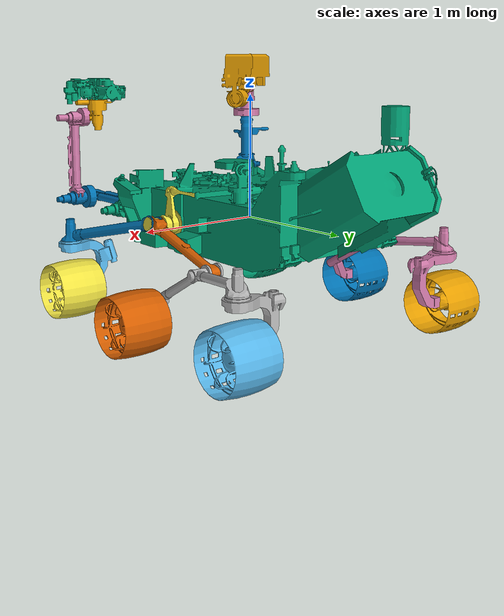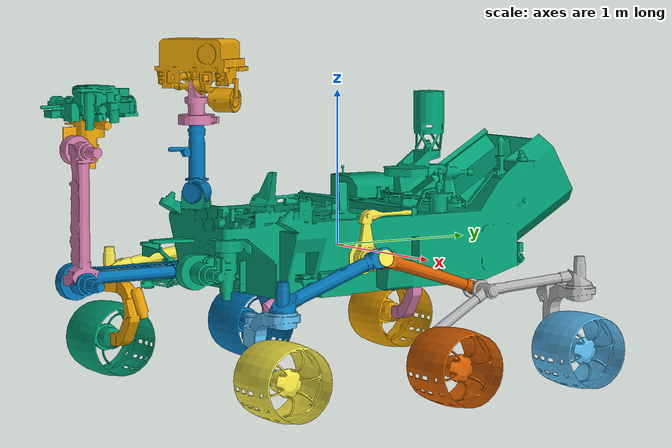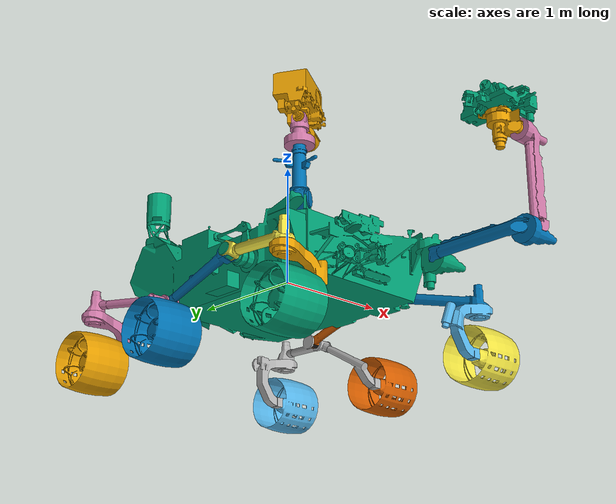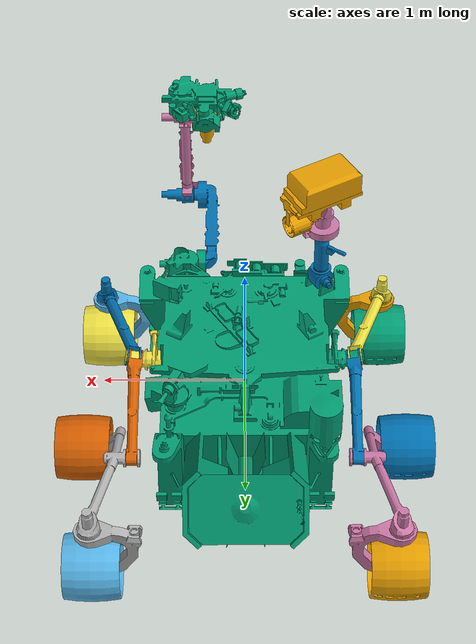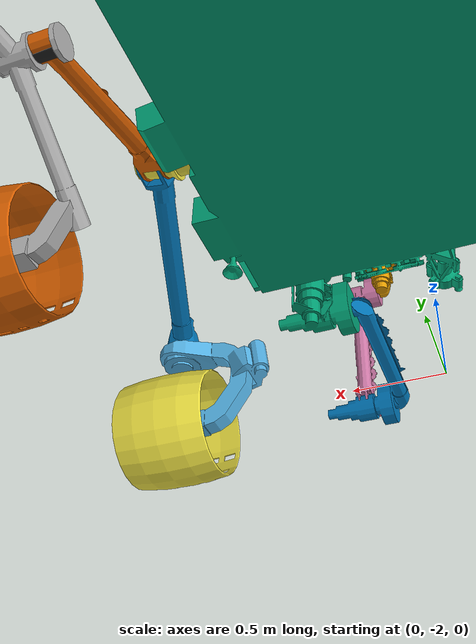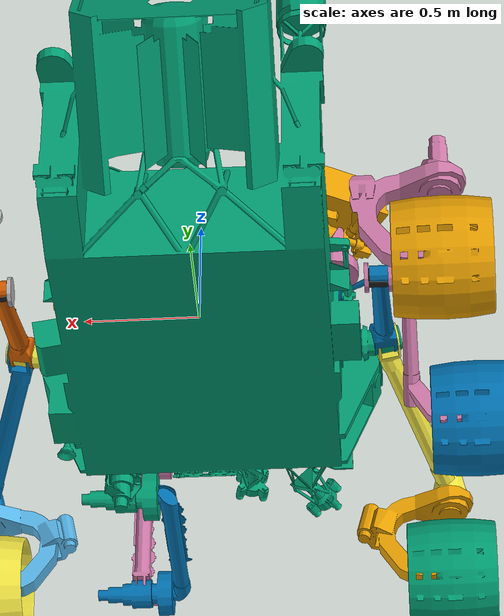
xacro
<?xml version="1.0"?>
<robot name="curiosity_mars_rover" xmlns:xacro="http://www.ros.org/wiki/xacro">

    <!-- Inertia matrices -->
	<xacro:include filename="$(find curiosity_mars_rover_description)/urdf/macros.xacro" />
	<!-- Robot constants and properties -->
	<xacro:include filename="$(find curiosity_mars_rover_description)/urdf/curiosity_mars_rover_properties.xacro" />
	<!-- Gazebo aspects of the robot -->
	<xacro:include filename="$(find curiosity_mars_rover_description)/urdf/curiosity_mars_rover.gazebo" />
	<!-- Chasis -->
	<xacro:include filename="$(find curiosity_mars_rover_description)/urdf/chassis.xacro" />
	<!-- Wheel Groups -->
	<xacro:include filename="$(find curiosity_mars_rover_description)/urdf/wheel.xacro" />
	<xacro:include filename="$(find curiosity_mars_rover_description)/urdf/left_wheel_group.xacro" />
	<xacro:include filename="$(find curiosity_mars_rover_description)/urdf/right_wheel_group.xacro" />
	<!-- Arm -->
	<xacro:include filename="$(find curiosity_mars_rover_description)/urdf/arm.xacro" />
	<!-- Sensor Mast -->
	<xacro:include filename="$(find curiosity_mars_rover_description)/urdf/sensor_mast.xacro" />

	<chassis_body/>
	<left_wheel_tree/>
	<right_wheel_tree/>

	<arm/>
	<sensor_mast/>

</robot>

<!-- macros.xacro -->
<!--
	definitions of some macros for easier description of the robot
-->

<robot xmlns:xacro="http://www.ros.org/wiki/xacro">

  <xacro:macro name="cylinder_inertia" params="m r h">

    <inertia
          ixx="${m*(3*r*r+h*h)/12}"
    			ixy = "0"
    			ixz = "0"
    			iyy="${m*(3*r*r+h*h)/12}"
    			iyz = "0"
    			izz="${m*r*r/2}"
    />
  </xacro:macro>

  <xacro:macro name="box_inertia" params="m x y z">

    <inertia
          ixx="${m*(y*y+z*z)/12}"
    			ixy = "0"
    			ixz = "0"
    			iyy="${m*(x*x+z*z)/12}"
    			iyz = "0"
    			izz="${m*(x*x+z*z)/12}"
    />
  </xacro:macro>

  <xacro:macro name="sphere_inertia" params="m r">

    <inertia
          ixx="${2*m*r*r/5}"
    			ixy = "0"
    			ixz = "0"
    			iyy="${2*m*r*r/5}"
    			iyz = "0"
    			izz="${2*m*r*r/5}"
    />
  </xacro:macro>

</robot>

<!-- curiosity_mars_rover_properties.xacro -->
<robot xmlns:xacro="http://www.ros.org/wiki/xacro">

	<!-- Constants -->
	<xacro:property name="PI" value="3.1415926535897931"/>

	<!-- Scaling -->
	<xacro:property name="scale_XYZ" value="1.0"/>

	<!-- Chassis properties -->
	<xacro:property name="chassisMass" value="733.64"/>

	<xacro:property name="chassisHeight" value="0.76"/>
	<xacro:property name="chassisLength" value="2.08157"/>
	<xacro:property name="chassisWidth" value="1.53774"/>

	<!-- Wheel Trees -->
	<xacro:property name="TreeMass" value="${72.96/2.0}"/>
	<xacro:property name="TreeParts" value="5.0"/>

	<xacro:property name="axisHeight" value="0.36388"/>
	<xacro:property name="axisLength" value="0.20321"/>
	<xacro:property name="axisWidth" value="0.27070"/>
	<xacro:property name="axisMass" value="${TreeMass/TreeParts}"/>

	<xacro:property name="suspension_arm_F_L_Mass" value="${TreeMass/TreeParts}"/>
	<xacro:property name="suspension_arm_F_L_X" value="0.39606"/>
	<xacro:property name="suspension_arm_F_L_Y" value="1.02203"/>
	<xacro:property name="suspension_arm_F_L_Z" value="0.30536"/>
	<xacro:property name="suspension_arm_F_L_limit" value="0.4"/>

	<xacro:property name="suspension_arm_B_L_Mass" value="${TreeMass/TreeParts}"/>
	<xacro:property name="suspension_arm_B_L_X" value="0.123524"/>
	<xacro:property name="suspension_arm_B_L_Y" value="0.852108"/>
	<xacro:property name="suspension_arm_B_L_Z" value="0.348354"/>
	<xacro:property name="suspension_arm_B_L_limit" value="0.4"/>

	<xacro:property name="suspension_arm_B2_L_Mass" value="${TreeMass/TreeParts}"/>
	<xacro:property name="suspension_arm_B2_L_X" value="0.400262"/>
	<xacro:property name="suspension_arm_B2_L_Y" value="1.22113"/>
	<xacro:property name="suspension_arm_B2_L_Z" value="0.631338"/>
	<xacro:property name="suspension_arm_B2_lower_limit" value="-1.2"/>
	<xacro:property name="suspension_arm_B2_upper_limit" value="0.1"/>

	<xacro:property name="suspension_steer_F_L_Mass" value="${TreeMass/TreeParts}"/>
	<xacro:property name="suspension_steer_F_L_X" value="0.528399"/>
	<xacro:property name="suspension_steer_F_L_Y" value="0.21019"/>
	<xacro:property name="suspension_steer_F_L_Z" value="0.450036"/>

	<xacro:property name="suspension_steer_B_L_Mass" value="${TreeMass/TreeParts}"/>
	<xacro:property name="suspension_steer_B_L_X" value="0.528399"/>
	<xacro:property name="suspension_steer_B_L_Y" value="0.21019"/>
	<xacro:property name="suspension_steer_B_L_Z" value="0.450036"/>

	<xacro:property name="suspension_steer_limit" value="0.6"/>
	<xacro:property name="suspension_steer_effort" value="10000.0"/>
	<xacro:property name="suspension_steer_velocity" value="10.0"/>

	<xacro:property name="suspension_effort" value="10000.0"/>
	<xacro:property name="suspension_speed" value="10.0"/>
	<xacro:property name="suspension_damping" value="0.5"/>
	<xacro:property name="suspension_friction" value="0.5"/>

	<!-- Wheels properties -->
	<xacro:property name="wheelWidth" value="0.39473"/>
	<xacro:property name="wheelRadius" value="0.242647"/>
	<xacro:property name="wheelMass" value="2.07"/>

	<!-- Arm -->
	<xacro:property name="armMass" value="30.0"/>
	<xacro:property name="armParts" value="5.0"/>

	<xacro:property name="arm_01_Mass" value="${armMass/armParts}"/>
	<xacro:property name="arm_01_X" value="0.356891"/>
	<xacro:property name="arm_01_Y" value="0.334128"/>
	<xacro:property name="arm_01_Z" value="0.300511"/>
	<xacro:property name="arm_01_limit" value="1.57"/>

	<xacro:property name="arm_02_Mass" value="${armMass/armParts}"/>
	<xacro:property name="arm_02_X" value="0.472171"/>
	<xacro:property name="arm_02_Y" value="0.972313"/>
	<xacro:property name="arm_02_Z" value="0.218611"/>
	<xacro:property name="arm_02_limit" value="1.57"/>

	<xacro:property name="arm_03_Mass" value="${armMass/armParts}"/>
	<xacro:property name="arm_03_X" value="0.30683"/>
	<xacro:property name="arm_03_Y" value="0.178607"/>
	<xacro:property name="arm_03_Z" value="0.878958"/>
	<xacro:property name="arm_03_limit" value="1.57"/>

	<xacro:property name="arm_04_Mass" value="${armMass/armParts}"/>
	<xacro:property name="arm_04_X" value="0.32452"/>
	<xacro:property name="arm_04_Y" value="0.344693"/>
	<xacro:property name="arm_04_Z" value="0.288832"/>
	<xacro:property name="arm_04_limit" value="1.57"/>

	<xacro:property name="arm_tools_Mass" value="${armMass/armParts}"/>
	<xacro:property name="arm_tools_X" value="0.60282"/>
	<xacro:property name="arm_tools_Y" value="0.467147"/>
	<xacro:property name="arm_tools_Z" value="0.21915"/>

	<!-- Mast -->
	<xacro:property name="mastMass" value="50.0"/>
	<xacro:property name="MastParts" value="3.0"/>

	<xacro:property name="mast_p_Mass" value="${mastMass/MastParts}"/>
	<xacro:property name="mast_p_X" value="0.192274"/>
	<xacro:property name="mast_p_Y" value="0.221494"/>
	<xacro:property name="mast_p_Z" value="0.525621"/>
	<xacro:property name="mast_p_upper_limit" value="1.57"/>
	<xacro:property name="mast_p_lower_limit" value="0.0"/>

	<xacro:property name="mast_02_Mass" value="${mastMass/MastParts}"/>
	<xacro:property name="mast_02_X" value="0.270963"/>
	<xacro:property name="mast_02_Y" value="0.232093"/>
	<xacro:property name="mast_02_Z" value="0.285976"/>

	<xacro:property name="mast_cameras_Mass" value="${mastMass/MastParts}"/>
	<xacro:property name="mast_cameras_X" value="0.550001"/>
	<xacro:property name="mast_cameras_Y" value="0.283001"/>
	<xacro:property name="mast_cameras_Z" value="0.203994"/>
	<xacro:property name="mast_cameras_limit" value="1.57"/>

</robot>

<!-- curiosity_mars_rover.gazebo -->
<robot xmlns:xacro="http://www.ros.org/wiki/xacro">

  <!-- ros_control plugin -->
  <gazebo>
    <plugin name="gazebo_ros_control"
            filename="libgazebo_ros_control.so">
      <robotNamespace>/curiosity_mars_rover</robotNamespace>
      <robotParam>/robot_description</robotParam>
      <robotSimType>gazebo_ros_control/DefaultRobotHWSim</robotSimType>
    </plugin>
  </gazebo>

  <gazebo>
    <plugin name="ground_truth"
            filename="libgazebo_ros_p3d.so">
      <frameName>world</frameName>
      <bodyName>chassis</bodyName>
      <topicName>/curiosity_mars_rover/odom</topicName>
      <updateRate>30.0</updateRate>
    </plugin>
  </gazebo>

  <gazebo reference="camera_link">
    <sensor type="depth" name="camera1">
      <update_rate>10.0</update_rate>
      <camera name="head">

        <pose>0 0 0 0 0 1.57</pose>

        <horizontal_fov>1.3962634</horizontal_fov>
        <image>
          <width>800</width>
          <height>800</height>
          <format>R8G8B8</format>
        </image>
        <clip>
          <near>0.01</near>
          <far>1000</far>
        </clip>
        <noise>
          <type>gaussian</type>
          <stddev>0.007</stddev>
        </noise>
      </camera>
      <plugin name="depthcamera_controller" filename="libgazebo_ros_openni_kinect.so">
        <baseline>.2</baseline>
        <alwaysOn>true</alwaysOn>
        <updateRate>1.0</updateRate>
        <cameraName>depthcamera</cameraName>
        <imageTopicName>/depthcamera/depth/image_raw</imageTopicName>
        <cameraInfoTopicName>/depthcamera/depth/camera_info</cameraInfoTopicName>
        <depthImageTopicName>/depthcamera/depth/image_raw</depthImageTopicName>
        <depthImageInfoTopicName>/depthcamera/depth/camera_info</depthImageInfoTopicName>
        <pointCloudTopicName>/depthcamera/depth/points</pointCloudTopicName>
        <frameName>pointcloud_link</frameName>
        <pointCloudCutoff>0.5</pointCloudCutoff>
        <pointCloudCutoffMax>300</pointCloudCutoffMax>
        <distortionK1>0.00000001</distortionK1>
        <distortionK2>0.00000001</distortionK2>
        <distortionK3>0.00000001</distortionK3>
        <distortionT1>0.00000001</distortionT1>
        <distortionT2>0.00000001</distortionT2>
        <CxPrime>0</CxPrime>
        <Cx>0</Cx>
        <Cy>0</Cy>
        <focalLength>0</focalLength>
        <hackBaseline>0</hackBaseline>
      </plugin>
    </sensor>
  </gazebo>

  <link name="pointcloud_link"/>
  <joint name="pointcloud_joint" type="fixed">
    <axis xyz="0 0 0" />
    <origin xyz="0 0 0" rpy="-1.58 0 0"/>
    <parent link="camera_link"/>
    <child link="pointcloud_link"/>
  </joint>

  <!-- stereo camera -->
    <gazebo reference="camera_link">
        <sensor type="multicamera" name="stereo_camera">
          <update_rate>10.0</update_rate>
          <camera name="left">
            <pose>0 0 0 0 0 1.57</pose>
            <horizontal_fov>1.3962634</horizontal_fov>
            <image>
              <width>800</width>
              <height>800</height>
              <format>R8G8B8</format>
            </image>
            <clip>
              <near>0.034</near>
              <far>100</far>
            </clip>
            <noise>
              <type>gaussian</type>
              <mean>0.0</mean>
              <stddev>0.007</stddev>
            </noise>
          </camera>
          <camera name="right">
            <pose>.25 0 0 0 0 1.57</pose>
            <horizontal_fov>1.3962634</horizontal_fov>
            <image>
              <width>800</width>
              <height>800</height>
              <format>R8G8B8</format>
            </image>
            <clip>
              <near>0.1</near>
              <far>100</far>
            </clip>
            <noise>
              <type>gaussian</type>
              <mean>0.0</mean>
              <stddev>0.007</stddev>
            </noise>
          </camera>
          <plugin name="stereo_camera_controller" filename="libgazebo_ros_multicamera.so">
            <alwaysOn>true</alwaysOn>
            <updateRate>0.0</updateRate>
            <cameraName>stereo/camera2</cameraName>
            <imageTopicName>image_raw</imageTopicName>
            <cameraInfoTopicName>camera_info</cameraInfoTopicName>
            <frameName>camera_link</frameName>
            <hackBaseline>0.07</hackBaseline>
            <distortionK1>0.0</distortionK1>
            <distortionK2>0.0</distortionK2>
            <distortionK3>0.0</distortionK3>
            <distortionT1>0.0</distortionT1>
            <distortionT2>0.0</distortionT2>
          </plugin>
        </sensor>
      </gazebo>

      <gazebo reference="chassis">
        <gravity>true</gravity>
        <sensor name="imu_sensor" type="imu">
          <always_on>true</always_on>
          <update_rate>100</update_rate>
          <visualize>true</visualize>
          <topic>__default_topic__</topic>
          <plugin filename="libgazebo_ros_imu_sensor.so" name="imu_plugin">
            <topicName>imu</topicName>
            <bodyName>imu_link</bodyName>
            <updateRateHZ>10.0</updateRateHZ>
            <gaussianNoise>0.0</gaussianNoise>
            <xyzOffset>0 0 0</xyzOffset>
            <rpyOffset>0 0 0</rpyOffset>
            <frameName>chassis</frameName>
            <initialOrientationAsReference>false</initialOrientationAsReference>
          </plugin>
          <pose>-0.032 0 0.068 0 0 3.14</pose>
        </sensor>
      </gazebo>

  <!-- Chassis -->
  <gazebo reference="chassis">
    <mu1>0.3</mu1>
    <mu2>0.3</mu2>
  </gazebo>

  <!-- Wheel Train -->
  <gazebo reference="left_axis">
    <mu1>0.3</mu1>
    <mu2>0.3</mu2>
  </gazebo>

  <gazebo reference="suspension_arm_F_L">
    <mu1>0.3</mu1>
    <mu2>0.3</mu2>
  </gazebo>

  <gazebo reference="right_axis">
    <mu1>0.3</mu1>
    <mu2>0.3</mu2>
  </gazebo>

  <gazebo reference="suspension_arm_F_R">
    <mu1>0.3</mu1>
    <mu2>0.3</mu2>
  </gazebo>

  <gazebo reference="suspension_arm_B_L">
    <mu1>0.3</mu1>
    <mu2>0.3</mu2>
  </gazebo>

  <gazebo reference="suspension_arm_B_R">
    <mu1>0.3</mu1>
    <mu2>0.3</mu2>
  </gazebo>

  <gazebo reference="suspension_arm_B_L_to_B2_L">
    <mu1>0.3</mu1>
    <mu2>0.3</mu2>
    <material>Gazebo/Black</material>
  </gazebo>

  <gazebo reference="suspension_arm_B_R_to_B2_R">
    <mu1>0.3</mu1>
    <mu2>0.3</mu2>
    <material>Gazebo/Black</material>
  </gazebo>

  <gazebo reference="suspension_arm_B2_L">
    <mu1>0.3</mu1>
    <mu2>0.3</mu2>
  </gazebo>

  <gazebo reference="suspension_arm_B2_R">
    <mu1>0.3</mu1>
    <mu2>0.3</mu2>
  </gazebo>

  <gazebo reference="suspension_arm_F_L_to_suspension_steer_F_L">
    <mu1>0.3</mu1>
    <mu2>0.3</mu2>
  </gazebo>

  <gazebo reference="suspension_arm_F_R_to_suspension_steer_F_R">
    <mu1>0.3</mu1>
    <mu2>0.3</mu2>
  </gazebo>

  <gazebo reference="suspension_steer_F_L">
    <mu1>0.3</mu1>
    <mu2>0.3</mu2>
  </gazebo>

    <gazebo reference="suspension_steer_F_R">
    <mu1>0.3</mu1>
    <mu2>0.3</mu2>
  </gazebo>

  <gazebo reference="suspension_arm_B2_L_to_suspension_steer_B_L">
    <mu1>0.3</mu1>
    <mu2>0.3</mu2>
  </gazebo>

  <gazebo reference="suspension_arm_B2_R_to_suspension_steer_B_R">
    <mu1>0.3</mu1>
    <mu2>0.3</mu2>
  </gazebo>

  <gazebo reference="suspension_steer_B_L">
    <mu1>0.3</mu1>
    <mu2>0.3</mu2>
  </gazebo>

  <gazebo reference="suspension_steer_B_R">
    <mu1>0.3</mu1>
    <mu2>0.3</mu2>
  </gazebo>

  <!-- Arm -->
  <gazebo reference="arm_01">
    <mu1>0.3</mu1>
    <mu2>0.3</mu2>
  </gazebo>

</robot>

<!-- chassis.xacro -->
<robot xmlns:xacro="http://www.ros.org/wiki/xacro">

  <xacro:macro name="chassis_body" params="">

    <!-- Used for fixing robot to Gazebo 'chassis' -->
	<link name="base_footprint" />

	<joint name="base_joint" type="fixed">
		<parent link="base_footprint"/>
		<child link="chassis"/>
	</joint>

	<link name='chassis'>

		<collision>
			<origin xyz="0 0 0"
					rpy="0 0 0"/>
			<geometry>
				<mesh filename="package://curiosity_mars_rover_description/meshes/chassis_full_fixed_glitch_v2.dae" scale="${scale_XYZ} ${scale_XYZ} ${scale_XYZ}"/>
			</geometry>
		</collision>

		<visual>
			<origin xyz="0 0 0"
					rpy="0 0 0"/>
			<geometry>
				<mesh filename="package://curiosity_mars_rover_description/meshes/chassis_full_fixed_glitch_v2.dae" scale="${scale_XYZ} ${scale_XYZ} ${scale_XYZ}"/>
			</geometry>
		</visual>

		<inertial>
			<origin xyz="0 0 0"
					rpy="0 0 0"/>
			<mass value="${chassisMass}"/>
			<box_inertia
				m="${chassisMass}"
				x="${chassisWidth*scale_XYZ}"
				y="${chassisLength*scale_XYZ}"
				z="${chassisHeight*scale_XYZ}"/>
		</inertial>

	</link>

  </xacro:macro>

</robot>

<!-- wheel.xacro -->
<robot xmlns:xacro="http://www.ros.org/wiki/xacro">

  <xacro:macro name="wheel" params="wheel_name wheel_conector_name tY">
    <!-- tY is Zero if left side, 1 if right side -->
    <link name='${wheel_name}'>
		<collision>
			<origin xyz="0 0 0"
					rpy="0 1.57 0"/>
			<geometry>
				<cylinder radius="${wheelRadius}" length="${wheelWidth}"/>
			</geometry>
		</collision>

		<visual>
			<origin xyz="0 0 0"
					rpy="0 0 0"/>
			<geometry>
				<mesh filename="package://curiosity_mars_rover_description/meshes/wheel_fixed.dae" scale="${scale_XYZ} ${scale_XYZ} ${scale_XYZ}"/>
			</geometry>
		</visual>

		<inertial>
			<origin xyz="0 0 0"
					rpy="0 0 0"/>
			<mass value="${wheelMass}"/>
			<cylinder_inertia
				m="${wheelMass}"
				r="${wheelRadius*scale_XYZ}"
				h="${wheelWidth*scale_XYZ}"/>
		</inertial>
	</link>

    <gazebo reference="${wheel_name}">
      <mu1 value="1.0"/>
      <mu2 value="1.0"/>
      <kp  value="10000000.0" />
      <kd>100.0</kd>
      <minDepth>0.001</minDepth>
      <maxVel>1.0</maxVel>
    </gazebo>

  	<joint name="${wheel_name}_joint" type="continuous">
		<parent link="${wheel_conector_name}"/>
		<child link="${wheel_name}"/>
		<origin xyz="0 0 0" rpy="0 0 ${tY*PI}"/>
		<limit effort="10000.0" velocity="100.0"/>
        <axis xyz="1 0 0"/>
        <joint_properties damping="0.0" friction="0.0"/>
	</joint>

    <transmission name="${wheel_name}_trans">
      <type>transmission_interface/SimpleTransmission</type>
      <joint name="${wheel_name}_joint">
        <hardwareInterface>hardware_interface/EffortJointInterface</hardwareInterface>
      </joint>
      <actuator name="${wheel_name}Motor">
        <hardwareInterface>hardware_interface/EffortJointInterface</hardwareInterface>
        <mechanicalReduction>1</mechanicalReduction>
      </actuator>
    </transmission>

  </xacro:macro>

</robot>

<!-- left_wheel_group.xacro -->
<robot xmlns:xacro="http://www.ros.org/wiki/xacro">

  <xacro:macro name="left_wheel_tree" params="">

  	<link name='left_axis'>

		<collision>
			<origin xyz="0 0 0"
					rpy="0 0 0"/>
			<geometry>
				<mesh filename="package://curiosity_mars_rover_description/meshes/left_axis_jointfix_v2.dae" scale="${scale_XYZ} ${scale_XYZ} ${scale_XYZ}"/>
			</geometry>
		</collision>

		<visual>
			<origin xyz="0 0 0"
					rpy="0 0 0"/>
			<geometry>
				<mesh filename="package://curiosity_mars_rover_description/meshes/left_axis_jointfix_v2.dae" scale="${scale_XYZ} ${scale_XYZ} ${scale_XYZ}"/>
			</geometry>
		</visual>

		<inertial>
			<origin xyz="0 0 0"
					rpy="0 0 0"/>
			<mass value="${axisMass}"/>
			<box_inertia
				m="${axisMass}"
				x="${axisWidth*scale_XYZ}"
				y="${axisLength*scale_XYZ}"
				z="${axisHeight*scale_XYZ}"/>
		</inertial>

	</link>

  	<joint name="left_axis_joint" type="fixed">
		<parent link="chassis"/>
		<child link="left_axis"/>
		<origin xyz="0.7938 -0.2133 0" rpy="0 -0.19565141 0"/>
	</joint>

  	<link name='suspension_arm_F_L'>
		<collision>
			<origin xyz="0 0 0"
					rpy="0 0 0"/>
			<geometry>
				<mesh filename="package://curiosity_mars_rover_description/meshes/suspension_arm_F_L_fixed.dae" scale="${scale_XYZ} ${scale_XYZ} ${scale_XYZ}"/>
			</geometry>
		</collision>

		<visual>
			<origin xyz="0 0 0"
					rpy="0 0 0"/>
			<geometry>
				<mesh filename="package://curiosity_mars_rover_description/meshes/suspension_arm_F_L_fixed.dae" scale="${scale_XYZ} ${scale_XYZ} ${scale_XYZ}"/>
			</geometry>
		</visual>

		<inertial>
			<origin xyz="0 0 0"
					rpy="0 0 0"/>
			<mass value="${suspension_arm_F_L_Mass}"/>
			<box_inertia
				m="${suspension_arm_F_L_Mass}"
				x="${suspension_arm_F_L_X*scale_XYZ}"
				y="${suspension_arm_F_L_Y*scale_XYZ}"
				z="${suspension_arm_F_L_Z*scale_XYZ}"/>
		</inertial>
	</link>

  	<joint name="suspension_arm_F_L_joint" type="revolute">
		<parent link="left_axis"/>
		<child link="suspension_arm_F_L"/>
		<origin xyz="0 0 0" rpy="0 0 0"/>
		<limit lower="${-suspension_arm_F_L_limit}" upper="${suspension_arm_F_L_limit}" effort="${suspension_effort}" velocity="${suspension_speed}"/>
        <axis xyz="1 0 0"/>
		<joint_properties damping="${suspension_damping}" friction="${suspension_friction}"/>
	</joint>

	<transmission name="suspension_arm_F_L_trans">
      <type>transmission_interface/SimpleTransmission</type>
      <joint name="suspension_arm_F_L_joint">
        <hardwareInterface>hardware_interface/EffortJointInterface</hardwareInterface>
      </joint>
      <actuator name="suspension_arm_F_LMotor">
        <hardwareInterface>hardware_interface/EffortJointInterface</hardwareInterface>
        <mechanicalReduction>1</mechanicalReduction>
      </actuator>
    </transmission>

  	<link name='suspension_arm_B_L'>
		<collision>
			<origin xyz="0 0 0"
					rpy="0 0 0"/>
			<geometry>
				<mesh filename="package://curiosity_mars_rover_description/meshes/suspension_arm_B_L_fixed.dae" scale="${scale_XYZ} ${scale_XYZ} ${scale_XYZ}"/>
			</geometry>
		</collision>

		<visual>
			<origin xyz="0 0 0"
					rpy="0 0 0"/>
			<geometry>
				<mesh filename="package://curiosity_mars_rover_description/meshes/suspension_arm_B_L_fixed.dae" scale="${scale_XYZ} ${scale_XYZ} ${scale_XYZ}"/>
			</geometry>
		</visual>

		<inertial>
			<origin xyz="0 0 0"
					rpy="0 0 0"/>
			<mass value="${suspension_arm_B_L_Mass}"/>
			<box_inertia
				m="${suspension_arm_B_L_Mass}"
				x="${suspension_arm_B_L_X*scale_XYZ}"
				y="${suspension_arm_B_L_Y*scale_XYZ}"
				z="${suspension_arm_B_L_Z*scale_XYZ}"/>
		</inertial>
	</link>

  	<joint name="suspension_arm_B_L_joint" type="revolute">
		<parent link="left_axis"/>
		<child link="suspension_arm_B_L"/>
		<origin xyz="0 0 0" rpy="0 0 0"/>
		<limit lower="${-suspension_arm_B_L_limit}" upper="${suspension_arm_B_L_limit}" effort="${suspension_effort}" velocity="${suspension_speed}"/>
        <axis xyz="1 0 0"/>
		<joint_properties damping="${suspension_damping}" friction="${suspension_friction}"/>
	</joint>

	<transmission name="suspension_arm_B_L_trans">
      <type>transmission_interface/SimpleTransmission</type>
      <joint name="suspension_arm_B_L_joint">
        <hardwareInterface>hardware_interface/EffortJointInterface</hardwareInterface>
      </joint>
      <actuator name="suspension_arm_B_LMotor">
        <hardwareInterface>hardware_interface/EffortJointInterface</hardwareInterface>
        <mechanicalReduction>1</mechanicalReduction>
      </actuator>
    </transmission>

 	<link name='suspension_arm_B_L_to_B2_L'>
		<inertial>
            <origin xyz="0 0 0" rpy="0 0 0"/>
            <mass value="0.02" />
            <inertia ixx="2.61666666667e-05" ixy="0.0" ixz="0.0" iyy="2.61666666667e-05" iyz="0.0" izz="3.6e-05"/>
        </inertial>
        <collision>
            <origin xyz="0 0 0.015" rpy="0 0 0"/>
            <geometry>
                <cylinder radius="0.06" length="0.035"/>
            </geometry>
        </collision>
		<visual>
            <origin rpy="0.0 1.57 0" xyz="0 0 0"/>
            <geometry>
                <cylinder radius="0.04" length="0.1"/>
            </geometry>
        </visual>
	</link>

	<joint name="suspension_arm_B_L_to_B2_L_joint" type="fixed">
		<parent link="suspension_arm_B_L"/>
		<child link="suspension_arm_B_L_to_B2_L"/>
		<origin xyz="-0.05159 0.73683 -0.22972" rpy="0 0.1937315 0"/>
	</joint>

	<link name='suspension_arm_B2_L'>
		<collision>
			<origin xyz="0 0 0"
					rpy="0 0 0"/>
			<geometry>
				<mesh filename="package://curiosity_mars_rover_description/meshes/suspension_arm_B2_L_fixed.dae" scale="${scale_XYZ} ${scale_XYZ} ${scale_XYZ}"/>
			</geometry>
		</collision>

		<visual>
			<origin xyz="0 0 0"
					rpy="0 0 0"/>
			<geometry>
				<mesh filename="package://curiosity_mars_rover_description/meshes/suspension_arm_B2_L_fixed.dae" scale="${scale_XYZ} ${scale_XYZ} ${scale_XYZ}"/>
			</geometry>
		</visual>

		<inertial>
			<origin xyz="0 0 0"
					rpy="0 0 0"/>
			<mass value="${suspension_arm_B2_L_Mass}"/>
			<box_inertia
				m="${suspension_arm_B2_L_Mass}"
				x="${suspension_arm_B2_L_X*scale_XYZ}"
				y="${suspension_arm_B2_L_Y*scale_XYZ}"
				z="${suspension_arm_B2_L_Z*scale_XYZ}"/>
		</inertial>
	</link>

  	<joint name="suspension_arm_B2_L_joint" type="revolute">
		<parent link="suspension_arm_B_L_to_B2_L"/>
		<child link="suspension_arm_B2_L"/>
		<origin xyz="0 0 0" rpy="0 0 0"/>
		<limit lower="${suspension_arm_B2_lower_limit}" upper="${suspension_arm_B2_upper_limit}" effort="${suspension_effort}" velocity="${suspension_speed}"/>
        <axis xyz="1 0 0"/>
		<joint_properties damping="${suspension_damping}" friction="${suspension_friction}"/>
	</joint>

	<transmission name="suspension_arm_B2_L_trans">
      <type>transmission_interface/SimpleTransmission</type>
      <joint name="suspension_arm_B2_L_joint">
        <hardwareInterface>hardware_interface/EffortJointInterface</hardwareInterface>
      </joint>
      <actuator name="suspension_arm_B2_LMotor">
        <hardwareInterface>hardware_interface/EffortJointInterface</hardwareInterface>
        <mechanicalReduction>1</mechanicalReduction>
      </actuator>
    </transmission>

	<!-- FRONT WHEEL -->
	<link name='suspension_arm_F_L_to_suspension_steer_F_L'>
		<inertial>
            <origin xyz="0 0 0" rpy="0 0 0"/>
            <mass value="0.02" />
            <inertia ixx="2.61666666667e-05" ixy="0.0" ixz="0.0" iyy="2.61666666667e-05" iyz="0.0" izz="3.6e-05"/>
        </inertial>
        <collision>
            <origin xyz="0 0 0.015" rpy="0 0 0"/>
            <geometry>
                <cylinder radius="0.06" length="0.04"/>
            </geometry>
        </collision>
		<visual>
            <origin rpy="0.0 0 0" xyz="0 0 0"/>
            <geometry>
                <cylinder radius="0.06" length="0.04"/>
            </geometry>
        </visual>
	</link>

	<joint name="suspension_arm_F_L_to_suspension_steer_F_L_joint" type="fixed">
		<parent link="suspension_arm_F_L"/>
		<child link="suspension_arm_F_L_to_suspension_steer_F_L"/>
		<origin xyz="0.2057 -0.87876 -0.29370" rpy="0 0.1937315 0"/>
	</joint>

	<link name='suspension_steer_F_L'>
		<collision>
			<origin xyz="0 0 0"
					rpy="0 0 0"/>
			<geometry>
				<mesh filename="package://curiosity_mars_rover_description/meshes/suspension_steer_F_L_fixed.dae" scale="${scale_XYZ} ${scale_XYZ} ${scale_XYZ}"/>
			</geometry>
		</collision>

		<visual>
			<origin xyz="0 0 0"
					rpy="0 0 0"/>
			<geometry>
				<mesh filename="package://curiosity_mars_rover_description/meshes/suspension_steer_F_L_fixed.dae" scale="${scale_XYZ} ${scale_XYZ} ${scale_XYZ}"/>
			</geometry>
		</visual>

		<inertial>
			<origin xyz="0 0 0"
					rpy="0 0 0"/>
			<mass value="${suspension_steer_F_L_Mass}"/>
			<box_inertia
				m="${suspension_steer_F_L_Mass}"
				x="${suspension_steer_F_L_X*scale_XYZ}"
				y="${suspension_steer_F_L_Y*scale_XYZ}"
				z="${suspension_steer_F_L_Z*scale_XYZ}"/>
		</inertial>
	</link>

  	<joint name="suspension_steer_F_L_joint" type="revolute">
		<parent link="suspension_arm_F_L_to_suspension_steer_F_L"/>
		<child link="suspension_steer_F_L"/>
		<origin xyz="0 0 0" rpy="0 0 0"/>
		<limit lower="${-suspension_steer_limit}" upper="${suspension_steer_limit}" effort="${suspension_steer_effort}" velocity="${suspension_steer_velocity}"/>
        <axis xyz="0 0 1"/>
	</joint>

	<transmission name="suspension_steer_F_L_trans">
      <type>transmission_interface/SimpleTransmission</type>
      <joint name="suspension_steer_F_L_joint">
        <hardwareInterface>hardware_interface/EffortJointInterface</hardwareInterface>
      </joint>
      <actuator name="suspension_steer_F_LMotor">
        <hardwareInterface>hardware_interface/EffortJointInterface</hardwareInterface>
        <mechanicalReduction>1</mechanicalReduction>
      </actuator>
    </transmission>

	<link name='suspension_steer_F_L_to_front_wheel_L'>
		<inertial>
            <origin xyz="0 0 0" rpy="0 0 0"/>
            <mass value="0.02" />
            <inertia ixx="2.61666666667e-05" ixy="0.0" ixz="0.0" iyy="2.61666666667e-05" iyz="0.0" izz="3.6e-05"/>
        </inertial>
        <collision>
            <origin rpy="0.0 1.57 0" xyz="0 0 0"/>
            <geometry>
                <cylinder radius="0.02" length="0.02"/>
            </geometry>
        </collision>
		<visual>
            <origin rpy="0.0 1.57 0" xyz="0 0 0"/>
            <geometry>
                <cylinder radius="0.02" length="0.02"/>
            </geometry>
        </visual>
	</link>

	<joint name="suspension_steer_F_L_to_suspension_steer_F_L_to_front_wheel_L_joint" type="fixed">
		<parent link="suspension_steer_F_L"/>
		<child link="suspension_steer_F_L_to_front_wheel_L"/>
		<origin xyz="0 0 -0.3996" rpy="0 0 0"/>
	</joint>

  	<wheel
		wheel_name="front_wheel_L"
		wheel_conector_name="suspension_steer_F_L_to_front_wheel_L"
		tY="0"/>

  	<!-- FRONT LEFT Wheel Left END -->

	<!-- MIDDLE WHEEL -->

	<link name='suspension_arm_B2_L_to_middle_wheel_L'>
		<inertial>
            <origin xyz="0 0 0" rpy="0 0 0"/>
            <mass value="0.02" />
            <inertia ixx="2.61666666667e-05" ixy="0.0" ixz="0.0" iyy="2.61666666667e-05" iyz="0.0" izz="3.6e-05"/>
        </inertial>
        <collision>
            <origin rpy="0.0 1.57 0" xyz="0 0 0"/>
            <geometry>
                <cylinder radius="0.02" length="0.02"/>
            </geometry>
        </collision>
		<visual>
            <origin rpy="0.0 1.57 0" xyz="0 0 0"/>
            <geometry>
                <cylinder radius="0.02" length="0.02"/>
            </geometry>
        </visual>
	</link>

	<joint name="suspension_arm_B2_L_to_suspension_arm_B2_L_to_middle_wheel_L_joint" type="fixed">
		<parent link="suspension_arm_B2_L"/>
		<child link="suspension_arm_B2_L_to_middle_wheel_L"/>
		<origin xyz="0.39423 -0.44859 -0.41098" rpy="0 0 0"/>
	</joint>

  	<wheel
		wheel_name="middle_wheel_L"
		wheel_conector_name="suspension_arm_B2_L_to_middle_wheel_L"
		tY="0"/>

  	<!-- FRONT MIDDLE Wheel Left END -->

	<!-- BACK WHEEL -->
	<link name='suspension_arm_B2_L_to_suspension_steer_B_L'>
		<inertial>
            <origin xyz="0 0 0" rpy="0 0 0"/>
            <mass value="0.02" />
            <inertia ixx="2.61666666667e-05" ixy="0.0" ixz="0.0" iyy="2.61666666667e-05" iyz="0.0" izz="3.6e-05"/>
        </inertial>
        <collision>
            <origin xyz="0 0 0.015" rpy="0 0 0"/>
            <geometry>
                <cylinder radius="0.06" length="0.04"/>
            </geometry>
        </collision>
		<visual>
            <origin rpy="0.0 0 0" xyz="0 0 0"/>
            <geometry>
                <cylinder radius="0.06" length="0.04"/>
            </geometry>
        </visual>
	</link>

	<joint name="suspension_arm_B2_L_to_suspension_steer_B_L_joint" type="fixed">
		<parent link="suspension_arm_B2_L"/>
		<child link="suspension_arm_B2_L_to_suspension_steer_B_L"/>
		<origin xyz="0.26271 0.62363 -0.00069" rpy="0 0 0"/>
	</joint>

	<link name='suspension_steer_B_L'>
		<collision>
			<origin xyz="0 0 0"
					rpy="0 0 0"/>
			<geometry>
				<mesh filename="package://curiosity_mars_rover_description/meshes/suspension_steer_B_L_fixed.dae" scale="${scale_XYZ} ${scale_XYZ} ${scale_XYZ}"/>
			</geometry>
		</collision>

		<visual>
			<origin xyz="0 0 0"
					rpy="0 0 0"/>
			<geometry>
				<mesh filename="package://curiosity_mars_rover_description/meshes/suspension_steer_B_L_fixed.dae" scale="${scale_XYZ} ${scale_XYZ} ${scale_XYZ}"/>
			</geometry>
		</visual>

		<inertial>
			<origin xyz="0 0 0"
					rpy="0 0 0"/>
			<mass value="${suspension_steer_B_L_Mass}"/>
			<box_inertia
				m="${suspension_steer_B_L_Mass}"
				x="${suspension_steer_B_L_X*scale_XYZ}"
				y="${suspension_steer_B_L_Y*scale_XYZ}"
				z="${suspension_steer_B_L_Z*scale_XYZ}"/>
		</inertial>
	</link>

  	<joint name="suspension_steer_B_L_joint" type="revolute">
		<parent link="suspension_arm_B2_L_to_suspension_steer_B_L"/>
		<child link="suspension_steer_B_L"/>
		<origin xyz="0 0 0" rpy="0 0 0"/>
		<limit lower="${-suspension_steer_limit}" upper="${suspension_steer_limit}" effort="${suspension_steer_effort}" velocity="${suspension_steer_velocity}"/>
        <axis xyz="0 0 1"/>
	</joint>

	<transmission name="suspension_steer_B_L_trans">
      <type>transmission_interface/SimpleTransmission</type>
      <joint name="suspension_steer_B_L_joint">
        <hardwareInterface>hardware_interface/EffortJointInterface</hardwareInterface>
      </joint>
      <actuator name="suspension_steer_B_LMotor">
        <hardwareInterface>hardware_interface/EffortJointInterface</hardwareInterface>
        <mechanicalReduction>1</mechanicalReduction>
      </actuator>
    </transmission>

  	<link name='suspension_steer_B_L_to_back_wheel_L'>
		<inertial>
            <origin xyz="0 0 0" rpy="0 0 0"/>
            <mass value="0.02" />
            <inertia ixx="2.61666666667e-05" ixy="0.0" ixz="0.0" iyy="2.61666666667e-05" iyz="0.0" izz="3.6e-05"/>
        </inertial>
        <collision>
            <origin rpy="0.0 1.57 0" xyz="0 0 0"/>
            <geometry>
                <cylinder radius="0.02" length="0.02"/>
            </geometry>
        </collision>
		<visual>
            <origin rpy="0.0 1.57 0" xyz="0 0 0"/>
            <geometry>
                <cylinder radius="0.02" length="0.02"/>
            </geometry>
        </visual>
	</link>

	<joint name="suspension_arm_B2_L_to_suspension_steer_B_L_to_back_wheel_L_joint" type="fixed">
		<parent link="suspension_steer_B_L"/>
		<child link="suspension_steer_B_L_to_back_wheel_L"/>
		<origin xyz="0 0 -0.410523" rpy="0 0 0"/>
	</joint>

  	<wheel
		wheel_name="back_wheel_L"
		wheel_conector_name="suspension_steer_B_L_to_back_wheel_L"
		tY="0"/>

  	<!-- END BACK WHEEL LEFT -->
  </xacro:macro>

</robot>

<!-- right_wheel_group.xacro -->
<robot xmlns:xacro="http://www.ros.org/wiki/xacro">

  <xacro:macro name="right_wheel_tree" params="">

  	<link name='right_axis'>
		<collision>
			<origin xyz="0 0 0"
					rpy="0 0 0"/>
			<geometry>
				<mesh filename="package://curiosity_mars_rover_description/meshes/right_axis_jointfix_v2.dae" scale="${scale_XYZ} ${scale_XYZ} ${scale_XYZ}"/>
			</geometry>
		</collision>

		<visual>
			<origin xyz="0 0 0"
					rpy="0 0 0"/>
			<geometry>
				<mesh filename="package://curiosity_mars_rover_description/meshes/right_axis_jointfix_v2.dae" scale="${scale_XYZ} ${scale_XYZ} ${scale_XYZ}"/>
			</geometry>
		</visual>

		<inertial>
			<origin xyz="0 0 0"
					rpy="0 0 0"/>
			<mass value="${axisMass}"/>
			<box_inertia
				m="${axisMass}"
				x="${axisWidth*scale_XYZ}"
				y="${axisLength*scale_XYZ}"
				z="${axisHeight*scale_XYZ}"/>
		</inertial>
	</link>

  	<joint name="right_axis_joint" type="fixed">
		<parent link="chassis"/>
		<child link="right_axis"/>
		<origin xyz="-0.7938 -0.2133 0" rpy="0 0.19565141 0"/>
	</joint>

	<link name='suspension_arm_F_R'>
		<collision>
			<origin xyz="0 0 0"
					rpy="0 0 0"/>
			<geometry>
				<mesh filename="package://curiosity_mars_rover_description/meshes/suspension_arm_F_R_fixed.dae" scale="${scale_XYZ} ${scale_XYZ} ${scale_XYZ}"/>
			</geometry>
		</collision>

		<visual>
			<origin xyz="0 0 0"
					rpy="0 0 0"/>
			<geometry>
				<mesh filename="package://curiosity_mars_rover_description/meshes/suspension_arm_F_R_fixed.dae" scale="${scale_XYZ} ${scale_XYZ} ${scale_XYZ}"/>
			</geometry>
		</visual>

		<inertial>
			<origin xyz="0 0 0"
					rpy="0 0 0"/>
			<mass value="${suspension_arm_F_L_Mass}"/>
			<box_inertia
				m="${suspension_arm_F_L_Mass}"
				x="${suspension_arm_F_L_X*scale_XYZ}"
				y="${suspension_arm_F_L_Y*scale_XYZ}"
				z="${suspension_arm_F_L_Z*scale_XYZ}"/>
		</inertial>
	</link>

  	<joint name="suspension_arm_F_R_joint" type="revolute">
		<parent link="right_axis"/>
		<child link="suspension_arm_F_R"/>
		<origin xyz="0 0 0" rpy="0 0 0"/>
		<limit lower="${-suspension_arm_F_L_limit}" upper="${suspension_arm_F_L_limit}" effort="${suspension_effort}" velocity="${suspension_speed}"/>
        <axis xyz="1 0 0"/>
		<joint_properties damping="${suspension_damping}" friction="${suspension_friction}"/>
	</joint>

  	<transmission name="suspension_arm_F_R_trans">
      <type>transmission_interface/SimpleTransmission</type>
      <joint name="suspension_arm_F_R_joint">
        <hardwareInterface>hardware_interface/EffortJointInterface</hardwareInterface>
      </joint>
      <actuator name="suspension_arm_F_RMotor">
        <hardwareInterface>hardware_interface/EffortJointInterface</hardwareInterface>
        <mechanicalReduction>1</mechanicalReduction>
      </actuator>
    </transmission>

  	<link name='suspension_arm_B_R'>
		<collision>
			<origin xyz="0 0 0"
					rpy="0 0 0"/>
			<geometry>
				<mesh filename="package://curiosity_mars_rover_description/meshes/suspension_arm_B_R_fixed.dae" scale="${scale_XYZ} ${scale_XYZ} ${scale_XYZ}"/>
			</geometry>
		</collision>

		<visual>
			<origin xyz="0 0 0"
					rpy="0 0 0"/>
			<geometry>
				<mesh filename="package://curiosity_mars_rover_description/meshes/suspension_arm_B_R_fixed.dae" scale="${scale_XYZ} ${scale_XYZ} ${scale_XYZ}"/>
			</geometry>
		</visual>

		<inertial>
			<origin xyz="0 0 0"
					rpy="0 0 0"/>
			<mass value="${suspension_arm_B_L_Mass}"/>
			<box_inertia
				m="${suspension_arm_B_L_Mass}"
				x="${suspension_arm_B_L_X*scale_XYZ}"
				y="${suspension_arm_B_L_Y*scale_XYZ}"
				z="${suspension_arm_B_L_Z*scale_XYZ}"/>
		</inertial>
	</link>

  	<joint name="suspension_arm_B_R_joint" type="revolute">
		<parent link="right_axis"/>
		<child link="suspension_arm_B_R"/>
		<origin xyz="0 0 0" rpy="0 0 0"/>
		<limit lower="${-suspension_arm_B_L_limit}" upper="${suspension_arm_B_L_limit}" effort="${suspension_effort}" velocity="${suspension_speed}"/>
        <axis xyz="1 0 0"/>
		<joint_properties damping="${suspension_damping}" friction="${suspension_friction}"/>
	</joint>

  	<transmission name="suspension_arm_B_R_trans">
      <type>transmission_interface/SimpleTransmission</type>
      <joint name="suspension_arm_B_R_joint">
        <hardwareInterface>hardware_interface/EffortJointInterface</hardwareInterface>
      </joint>
      <actuator name="suspension_arm_B_RMotor">
        <hardwareInterface>hardware_interface/EffortJointInterface</hardwareInterface>
        <mechanicalReduction>1</mechanicalReduction>
      </actuator>
    </transmission>

  	<link name='suspension_arm_B_R_to_B2_R'>
		<inertial>
            <origin xyz="0 0 0" rpy="0 0 0"/>
            <mass value="0.02" />
            <inertia ixx="2.61666666667e-05" ixy="0.0" ixz="0.0" iyy="2.61666666667e-05" iyz="0.0" izz="3.6e-05"/>
        </inertial>
        <collision>
            <origin xyz="0 0 0.015" rpy="0 0 0"/>
            <geometry>
                <cylinder radius="0.06" length="0.035"/>
            </geometry>
        </collision>
		<visual>
            <origin rpy="0.0 1.57 0" xyz="0 0 0"/>
            <geometry>
                <cylinder radius="0.04" length="0.1"/>
            </geometry>
        </visual>
	</link>

	<joint name="suspension_arm_B_R_to_B2_R_joint" type="fixed">
		<parent link="suspension_arm_B_R"/>
		<child link="suspension_arm_B_R_to_B2_R"/>
		<origin xyz="0.05159 0.73683 -0.22972" rpy="0 -0.1937315 0"/>
	</joint>

	<link name='suspension_arm_B2_R'>
		<collision>
			<origin xyz="0 0 0"
					rpy="0 0 0"/>
			<geometry>
				<mesh filename="package://curiosity_mars_rover_description/meshes/suspension_arm_B2_R_fixed.dae" scale="${scale_XYZ} ${scale_XYZ} ${scale_XYZ}"/>
			</geometry>
		</collision>

		<visual>
			<origin xyz="0 0 0"
					rpy="0 0 0"/>
			<geometry>
				<mesh filename="package://curiosity_mars_rover_description/meshes/suspension_arm_B2_R_fixed.dae" scale="${scale_XYZ} ${scale_XYZ} ${scale_XYZ}"/>
			</geometry>
		</visual>

		<inertial>
			<origin xyz="0 0 0"
					rpy="0 0 0"/>
			<mass value="${suspension_arm_B2_L_Mass}"/>
			<box_inertia
				m="${suspension_arm_B2_L_Mass}"
				x="${suspension_arm_B2_L_X*scale_XYZ}"
				y="${suspension_arm_B2_L_Y*scale_XYZ}"
				z="${suspension_arm_B2_L_Z*scale_XYZ}"/>
		</inertial>
	</link>

  	<joint name="suspension_arm_B2_R_joint" type="revolute">
		<parent link="suspension_arm_B_R_to_B2_R"/>
		<child link="suspension_arm_B2_R"/>
		<origin xyz="0 0 0" rpy="0 0 0"/>
		<limit lower="${suspension_arm_B2_lower_limit}" upper="${suspension_arm_B2_upper_limit}" effort="${suspension_effort}" velocity="${suspension_speed}"/>
        <axis xyz="1 0 0"/>
		<joint_properties damping="${suspension_damping}" friction="${suspension_friction}"/>
	</joint>

  	<transmission name="suspension_arm_B2_R_trans">
      <type>transmission_interface/SimpleTransmission</type>
      <joint name="suspension_arm_B2_R_joint">
        <hardwareInterface>hardware_interface/EffortJointInterface</hardwareInterface>
      </joint>
      <actuator name="suspension_arm_B2_RMotor">
        <hardwareInterface>hardware_interface/EffortJointInterface</hardwareInterface>
        <mechanicalReduction>1</mechanicalReduction>
      </actuator>
    </transmission>

	<!-- FRONT WHEEL RIGHT -->

	<link name='suspension_arm_F_R_to_suspension_steer_F_R'>
		<inertial>
            <origin xyz="0 0 0" rpy="0 0 0"/>
            <mass value="0.02" />
            <inertia ixx="2.61666666667e-05" ixy="0.0" ixz="0.0" iyy="2.61666666667e-05" iyz="0.0" izz="3.6e-05"/>
        </inertial>
        <collision>
            <origin xyz="0 0 0.015" rpy="0 0 0"/>
            <geometry>
                <cylinder radius="0.06" length="0.04"/>
            </geometry>
        </collision>
		<visual>
            <origin rpy="0.0 0 0" xyz="0 0 0"/>
            <geometry>
                <cylinder radius="0.06" length="0.04"/>
            </geometry>
        </visual>
	</link>

	<joint name="suspension_arm_F_R_to_suspension_steer_F_R_joint" type="fixed">
		<parent link="suspension_arm_F_R"/>
		<child link="suspension_arm_F_R_to_suspension_steer_F_R"/>
		<origin xyz="-0.2057 -0.87876 -0.29370" rpy="0 -0.1937315 0"/>
	</joint>

	<link name='suspension_steer_F_R'>
		<collision>
			<origin xyz="0 0 0"
					rpy="0 0 0"/>
			<geometry>
				<mesh filename="package://curiosity_mars_rover_description/meshes/suspension_steer_F_R_fixed.dae" scale="${scale_XYZ} ${scale_XYZ} ${scale_XYZ}"/>
			</geometry>
		</collision>

		<visual>
			<origin xyz="0 0 0"
					rpy="0 0 0"/>
			<geometry>
				<mesh filename="package://curiosity_mars_rover_description/meshes/suspension_steer_F_R_fixed.dae" scale="${scale_XYZ} ${scale_XYZ} ${scale_XYZ}"/>
			</geometry>
		</visual>

		<inertial>
			<origin xyz="0 0 0"
					rpy="0 0 0"/>
			<mass value="${suspension_steer_F_L_Mass}"/>
			<box_inertia
				m="${suspension_steer_F_L_Mass}"
				x="${suspension_steer_F_L_X*scale_XYZ}"
				y="${suspension_steer_F_L_Y*scale_XYZ}"
				z="${suspension_steer_F_L_Z*scale_XYZ}"/>
		</inertial>
	</link>

  	<joint name="suspension_steer_F_R_joint" type="revolute">
		<parent link="suspension_arm_F_R_to_suspension_steer_F_R"/>
		<child link="suspension_steer_F_R"/>
		<origin xyz="0 0 0" rpy="0 0 0"/>
		<limit lower="${-suspension_steer_limit}" upper="${suspension_steer_limit}" effort="${suspension_steer_effort}" velocity="${suspension_steer_velocity}"/>
        <axis xyz="0 0 1"/>
	</joint>

	<transmission name="suspension_steer_F_R_trans">
      <type>transmission_interface/SimpleTransmission</type>
      <joint name="suspension_steer_F_R_joint">
        <hardwareInterface>hardware_interface/EffortJointInterface</hardwareInterface>
      </joint>
      <actuator name="suspension_steer_F_RMotor">
        <hardwareInterface>hardware_interface/EffortJointInterface</hardwareInterface>
        <mechanicalReduction>1</mechanicalReduction>
      </actuator>
    </transmission>

	<link name='suspension_steer_F_R_to_front_wheel_R'>
		<inertial>
            <origin xyz="0 0 0" rpy="0 0 0"/>
            <mass value="0.02" />
            <inertia ixx="2.61666666667e-05" ixy="0.0" ixz="0.0" iyy="2.61666666667e-05" iyz="0.0" izz="3.6e-05"/>
        </inertial>
        <collision>
            <origin rpy="0.0 1.57 0" xyz="0 0 0"/>
            <geometry>
                <cylinder radius="0.02" length="0.02"/>
            </geometry>
        </collision>
		<visual>
            <origin rpy="0.0 1.57 0" xyz="0 0 0"/>
            <geometry>
                <cylinder radius="0.02" length="0.02"/>
            </geometry>
        </visual>
	</link>

	<joint name="suspension_steer_F_R_to_suspension_steer_F_R_to_front_wheel_R_joint" type="fixed">
		<parent link="suspension_steer_F_R"/>
		<child link="suspension_steer_F_R_to_front_wheel_R"/>
		<origin xyz="0 0 -0.3996" rpy="0 0 0"/>
	</joint>

  	<wheel
		wheel_name="front_wheel_R"
		wheel_conector_name="suspension_steer_F_R_to_front_wheel_R"
		tY="-1"/>

  	<!-- FRONT WHEEL RIGHT END -->

	<link name='suspension_arm_B2_R_to_middle_wheel_R'>
		<inertial>
            <origin xyz="0 0 0" rpy="0 0 0"/>
            <mass value="0.02" />
            <inertia ixx="2.61666666667e-05" ixy="0.0" ixz="0.0" iyy="2.61666666667e-05" iyz="0.0" izz="3.6e-05"/>
        </inertial>
        <collision>
            <origin rpy="0.0 1.57 0" xyz="0 0 0"/>
            <geometry>
                <cylinder radius="0.02" length="0.02"/>
            </geometry>
        </collision>
		<visual>
            <origin rpy="0.0 1.57 0" xyz="0 0 0"/>
            <geometry>
                <cylinder radius="0.02" length="0.02"/>
            </geometry>
        </visual>
	</link>

	<joint name="suspension_arm_B2_R_to_suspension_arm_B2_R_to_middle_wheel_R_joint" type="fixed">
		<parent link="suspension_arm_B2_R"/>
		<child link="suspension_arm_B2_R_to_middle_wheel_R"/>
		<origin xyz="-0.39423 -0.44859 -0.41098" rpy="0 0 0"/>
	</joint>

  	<wheel
		wheel_name="middle_wheel_R"
		wheel_conector_name="suspension_arm_B2_R_to_middle_wheel_R"
		tY="-1"/>

  	<!-- RIGHT BACK WHEEL -->
	<link name='suspension_arm_B2_R_to_suspension_steer_B_R'>
		<inertial>
            <origin xyz="0 0 0" rpy="0 0 0"/>
            <mass value="0.02" />
            <inertia ixx="2.61666666667e-05" ixy="0.0" ixz="0.0" iyy="2.61666666667e-05" iyz="0.0" izz="3.6e-05"/>
        </inertial>
        <collision>
            <origin xyz="0 0 0.015" rpy="0 0 0"/>
            <geometry>
                <cylinder radius="0.06" length="0.04"/>
            </geometry>
        </collision>
		<visual>
            <origin rpy="0.0 0 0" xyz="0 0 0"/>
            <geometry>
                <cylinder radius="0.06" length="0.04"/>
            </geometry>
        </visual>
	</link>

	<joint name="suspension_arm_B2_R_to_suspension_steer_B_R_joint" type="fixed">
		<parent link="suspension_arm_B2_R"/>
		<child link="suspension_arm_B2_R_to_suspension_steer_B_R"/>
		<origin xyz="-0.26271 0.62363 -0.00069" rpy="0 0 0"/>
	</joint>

	<link name='suspension_steer_B_R'>
		<collision>
			<origin xyz="0 0 0"
					rpy="0 0 0"/>
			<geometry>
				<mesh filename="package://curiosity_mars_rover_description/meshes/suspension_steer_B_R_fixed.dae" scale="${scale_XYZ} ${scale_XYZ} ${scale_XYZ}"/>
			</geometry>
		</collision>

		<visual>
			<origin xyz="0 0 0"
					rpy="0 0 0"/>
			<geometry>
				<mesh filename="package://curiosity_mars_rover_description/meshes/suspension_steer_B_R_fixed.dae" scale="${scale_XYZ} ${scale_XYZ} ${scale_XYZ}"/>
			</geometry>
		</visual>

		<inertial>
			<origin xyz="0 0 0"
					rpy="0 0 0"/>
			<mass value="${suspension_steer_B_L_Mass}"/>
			<box_inertia
				m="${suspension_steer_B_L_Mass}"
				x="${suspension_steer_B_L_X*scale_XYZ}"
				y="${suspension_steer_B_L_Y*scale_XYZ}"
				z="${suspension_steer_B_L_Z*scale_XYZ}"/>
		</inertial>
	</link>

  	<joint name="suspension_steer_B_R_joint" type="revolute">
		<parent link="suspension_arm_B2_R_to_suspension_steer_B_R"/>
		<child link="suspension_steer_B_R"/>
		<origin xyz="0 0 0" rpy="0 0 0"/>
		<limit lower="${-suspension_steer_limit}" upper="${suspension_steer_limit}" effort="${suspension_steer_effort}" velocity="${suspension_steer_velocity}"/>
        <axis xyz="0 0 1"/>
	</joint>

  	<transmission name="suspension_steer_B_R_trans">
      <type>transmission_interface/SimpleTransmission</type>
      <joint name="suspension_steer_B_R_joint">
        <hardwareInterface>hardware_interface/EffortJointInterface</hardwareInterface>
      </joint>
      <actuator name="suspension_steer_B_RMotor">
        <hardwareInterface>hardware_interface/EffortJointInterface</hardwareInterface>
        <mechanicalReduction>1</mechanicalReduction>
      </actuator>
    </transmission>

	<link name='suspension_steer_B_R_to_back_wheel_R'>
		<inertial>
            <origin xyz="0 0 0" rpy="0 0 0"/>
            <mass value="0.02" />
            <inertia ixx="2.61666666667e-05" ixy="0.0" ixz="0.0" iyy="2.61666666667e-05" iyz="0.0" izz="3.6e-05"/>
        </inertial>
        <collision>
            <origin rpy="0.0 1.57 0" xyz="0 0 0"/>
            <geometry>
                <cylinder radius="0.02" length="0.02"/>
            </geometry>
        </collision>
		<visual>
            <origin rpy="0.0 1.57 0" xyz="0 0 0"/>
            <geometry>
                <cylinder radius="0.02" length="0.02"/>
            </geometry>
        </visual>
	</link>

	<joint name="suspension_arm_B2_R_to_suspension_steer_B_R_to_back_wheel_R_joint" type="fixed">
		<parent link="suspension_steer_B_R"/>
		<child link="suspension_steer_B_R_to_back_wheel_R"/>
		<origin xyz="0 0 -0.410523" rpy="0 0 0"/>
	</joint>

  	<wheel
		wheel_name="back_wheel_R"
		wheel_conector_name="suspension_steer_B_R_to_back_wheel_R"
		tY="-1"/>

  	<!-- END BACK WHEEL RIGHT -->

  </xacro:macro>

</robot>

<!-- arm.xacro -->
<robot xmlns:xacro="http://www.ros.org/wiki/xacro">

  <xacro:macro name="arm" params="">

	<link name='chassis_to_arm_01'>
		<inertial>
            <origin xyz="0 0 0" rpy="0 0 0"/>
            <mass value="0.02" />
            <inertia ixx="2.61666666667e-05" ixy="0.0" ixz="0.0" iyy="2.61666666667e-05" iyz="0.0" izz="3.6e-05"/>
        </inertial>
        <collision>
            <origin rpy="0.0 1.57 0" xyz="0 0 0"/>
            <geometry>
                <cylinder radius="0.02" length="0.02"/>
            </geometry>
        </collision>
		<visual>
            <origin rpy="0.0 0 0" xyz="0 0 0"/>
            <geometry>
                <cylinder radius="0.02" length="0.02"/>
            </geometry>
        </visual>
	</link>

	<joint name="chassis_to_arm_01_joint" type="fixed">
		<parent link="chassis"/>
		<child link="chassis_to_arm_01"/>
		<origin xyz="0.449641 -1.11319 0.112807" rpy="0 0 0"/>
	</joint>

	<link name='arm_01'>
		<collision>
			<origin xyz="0 0 0"
					rpy="0 0 0"/>
			<geometry>
				<mesh filename="package://curiosity_mars_rover_description/meshes/arm_01_fixed.dae" scale="${scale_XYZ} ${scale_XYZ} ${scale_XYZ}"/>
			</geometry>
		</collision>

		<visual>
			<origin xyz="0 0 0"
					rpy="0 0 0"/>
			<geometry>
				<mesh filename="package://curiosity_mars_rover_description/meshes/arm_01_fixed.dae" scale="${scale_XYZ} ${scale_XYZ} ${scale_XYZ}"/>
			</geometry>
		</visual>

		<inertial>
			<origin xyz="0 0 0"
					rpy="0 0 0"/>
			<mass value="${arm_01_Mass}"/>
			<box_inertia
				m="${arm_01_Mass}"
				x="${arm_01_X*scale_XYZ}"
				y="${arm_01_Y*scale_XYZ}"
				z="${arm_01_Z*scale_XYZ}"/>
		</inertial>
	</link>

  	<joint name="arm_01_joint" type="revolute">
		<parent link="chassis_to_arm_01"/>
		<child link="arm_01"/>
		<origin xyz="0 0 0" rpy="0 0 0"/>
		<limit lower="${-arm_01_limit}" upper="${arm_01_limit}" effort="10000.0" velocity="100.0"/>
        <axis xyz="0 0 1"/>
        <joint_properties damping="0.0" friction="0.0"/>
	</joint>

    <transmission name="arm_01_trans">
      <type>transmission_interface/SimpleTransmission</type>
      <joint name="arm_01_joint">
        <hardwareInterface>hardware_interface/EffortJointInterface</hardwareInterface>
      </joint>
      <actuator name="arm_01Motor">
        <hardwareInterface>hardware_interface/EffortJointInterface</hardwareInterface>
        <mechanicalReduction>1</mechanicalReduction>
      </actuator>
    </transmission>

  	<link name='arm_01_to_arm_02'>
		<inertial>
            <origin xyz="0 0 0" rpy="0 0 0"/>
            <mass value="0.02" />
            <inertia ixx="2.61666666667e-05" ixy="0.0" ixz="0.0" iyy="2.61666666667e-05" iyz="0.0" izz="3.6e-05"/>
        </inertial>
        <collision>
            <origin rpy="0.0 1.57 0" xyz="0 0 0"/>
            <geometry>
                <cylinder radius="0.02" length="0.02"/>
            </geometry>
        </collision>
		<visual>
            <origin rpy="0.0 0 0" xyz="0 0 0"/>
            <geometry>
                <cylinder radius="0.02" length="0.02"/>
            </geometry>
        </visual>
	</link>

	<joint name="arm_01_to_arm_02_joint" type="fixed">
		<parent link="arm_01"/>
		<child link="arm_01_to_arm_02"/>
		<origin xyz="0.0 -0.160259 -0.166117" rpy="0 0 0"/>
	</joint>

	<link name='arm_02'>
		<collision>
			<origin xyz="0 0 0"
					rpy="0 0 0"/>
			<geometry>
				<mesh filename="package://curiosity_mars_rover_description/meshes/arm_02_fixed.dae" scale="${scale_XYZ} ${scale_XYZ} ${scale_XYZ}"/>
			</geometry>
		</collision>

		<visual>
			<origin xyz="0 0 0"
					rpy="0 0 0"/>
			<geometry>
				<mesh filename="package://curiosity_mars_rover_description/meshes/arm_02_fixed.dae" scale="${scale_XYZ} ${scale_XYZ} ${scale_XYZ}"/>
			</geometry>
		</visual>

		<inertial>
			<origin xyz="0 0 0"
					rpy="0 0 0"/>
			<mass value="${arm_02_Mass}"/>
			<box_inertia
				m="${arm_02_Mass}"
				x="${arm_02_X*scale_XYZ}"
				y="${arm_02_Y*scale_XYZ}"
				z="${arm_02_Z*scale_XYZ}"/>
		</inertial>
	</link>

  	<joint name="arm_02_joint" type="revolute">
		<parent link="arm_01_to_arm_02"/>
		<child link="arm_02"/>
		<origin xyz="0 0 0" rpy="0 0 0"/>
		<limit lower="${-arm_02_limit}" upper="${arm_02_limit}" effort="10000.0" velocity="100.0"/>
        <axis xyz="1 0 0"/>
        <joint_properties damping="0.0" friction="0.0"/>
	</joint>

    <transmission name="arm_02_trans">
      <type>transmission_interface/SimpleTransmission</type>
      <joint name="arm_02_joint">
        <hardwareInterface>hardware_interface/EffortJointInterface</hardwareInterface>
      </joint>
      <actuator name="arm_02Motor">
        <hardwareInterface>hardware_interface/EffortJointInterface</hardwareInterface>
        <mechanicalReduction>1</mechanicalReduction>
      </actuator>
    </transmission>

  	<link name='arm_02_to_arm_03'>
		<inertial>
            <origin xyz="0 0 0" rpy="0 0 0"/>
            <mass value="0.02" />
            <inertia ixx="2.61666666667e-05" ixy="0.0" ixz="0.0" iyy="2.61666666667e-05" iyz="0.0" izz="3.6e-05"/>
        </inertial>
        <collision>
            <origin rpy="0.0 1.57 0" xyz="0 0 0"/>
            <geometry>
                <cylinder radius="0.02" length="0.02"/>
            </geometry>
        </collision>
		<visual>
            <origin rpy="0.0 0 0" xyz="0 0 0"/>
            <geometry>
                <cylinder radius="0.02" length="0.02"/>
            </geometry>
        </visual>
	</link>

	<joint name="arm_02_to_arm_03_joint" type="fixed">
		<parent link="arm_02"/>
		<child link="arm_02_to_arm_03"/>
		<origin xyz="0.071249 -0.825069 0.0" rpy="0 0 0"/>
	</joint>

  	<link name='arm_03'>
		<collision>
			<origin xyz="0 0 0"
					rpy="0 0 0"/>
			<geometry>
				<mesh filename="package://curiosity_mars_rover_description/meshes/arm_03_fixed.dae" scale="${scale_XYZ} ${scale_XYZ} ${scale_XYZ}"/>
			</geometry>
		</collision>

		<visual>
			<origin xyz="0 0 0"
					rpy="0 0 0"/>
			<geometry>
				<mesh filename="package://curiosity_mars_rover_description/meshes/arm_03_fixed.dae" scale="${scale_XYZ} ${scale_XYZ} ${scale_XYZ}"/>
			</geometry>
		</visual>

		<inertial>
			<origin xyz="0 0 0"
					rpy="0 0 0"/>
			<mass value="${arm_03_Mass}"/>
			<box_inertia
				m="${arm_03_Mass}"
				x="${arm_03_X*scale_XYZ}"
				y="${arm_03_Y*scale_XYZ}"
				z="${arm_03_Z*scale_XYZ}"/>
		</inertial>
	</link>

  	<joint name="arm_03_joint" type="revolute">
		<parent link="arm_02_to_arm_03"/>
		<child link="arm_03"/>
		<origin xyz="0 0 0" rpy="0 0 0"/>
		<limit lower="${-arm_03_limit}" upper="${arm_03_limit}" effort="10000.0" velocity="100.0"/>
        <axis xyz="1 0 0"/>
        <joint_properties damping="0.0" friction="0.0"/>
	</joint>

    <transmission name="arm_03_trans">
      <type>transmission_interface/SimpleTransmission</type>
      <joint name="arm_03_joint">
        <hardwareInterface>hardware_interface/EffortJointInterface</hardwareInterface>
      </joint>
      <actuator name="arm_03Motor">
        <hardwareInterface>hardware_interface/EffortJointInterface</hardwareInterface>
        <mechanicalReduction>1</mechanicalReduction>
      </actuator>
    </transmission>

  	<link name='arm_03_to_arm_04'>
		<inertial>
            <origin xyz="0 0 0" rpy="0 0 0"/>
            <mass value="0.02" />
            <inertia ixx="2.61666666667e-05" ixy="0.0" ixz="0.0" iyy="2.61666666667e-05" iyz="0.0" izz="3.6e-05"/>
        </inertial>
        <collision>
            <origin rpy="1.57 0 0" xyz="0 0 0"/>
            <geometry>
                <cylinder radius="0.02" length="0.02"/>
            </geometry>
        </collision>
		<visual>
            <origin rpy="1.57 0 0" xyz="0 0 0"/>
            <geometry>
                <cylinder radius="0.02" length="0.02"/>
            </geometry>
        </visual>
	</link>

	<joint name="arm_03_to_arm_04_joint" type="fixed">
		<parent link="arm_03"/>
		<child link="arm_03_to_arm_04"/>
		<origin xyz="-0.193815 0.0 0.779746" rpy="0 0 ${PI/2.0}"/>
	</joint>

  	<link name='arm_04'>
		<collision>
			<origin xyz="0 0 0"
					rpy="0 0 0"/>
			<geometry>
				<mesh filename="package://curiosity_mars_rover_description/meshes/arm_04_fixed.dae" scale="${scale_XYZ} ${scale_XYZ} ${scale_XYZ}"/>
			</geometry>
		</collision>

		<visual>
			<origin xyz="0 0 0"
					rpy="0 0 0"/>
			<geometry>
				<mesh filename="package://curiosity_mars_rover_description/meshes/arm_04_fixed.dae" scale="${scale_XYZ} ${scale_XYZ} ${scale_XYZ}"/>
			</geometry>
		</visual>

		<inertial>
			<origin xyz="0 0 0"
					rpy="0 0 0"/>
			<mass value="${arm_04_Mass}"/>
			<box_inertia
				m="${arm_04_Mass}"
				x="${arm_04_X*scale_XYZ}"
				y="${arm_04_Y*scale_XYZ}"
				z="${arm_04_Z*scale_XYZ}"/>
		</inertial>
	</link>

  	<joint name="arm_04_joint" type="revolute">
		<parent link="arm_03_to_arm_04"/>
		<child link="arm_04"/>
		<origin xyz="0 0 0" rpy="0 0 0"/>
		<limit lower="${-arm_04_limit}" upper="${arm_04_limit}" effort="10000.0" velocity="100.0"/>
        <axis xyz="0 1 0"/>
        <joint_properties damping="0.0" friction="0.0"/>
	</joint>

    <transmission name="arm_04_trans">
      <type>transmission_interface/SimpleTransmission</type>
      <joint name="arm_04_joint">
        <hardwareInterface>hardware_interface/EffortJointInterface</hardwareInterface>
      </joint>
      <actuator name="arm_04Motor">
        <hardwareInterface>hardware_interface/EffortJointInterface</hardwareInterface>
        <mechanicalReduction>1</mechanicalReduction>
      </actuator>
    </transmission>

  	<link name='arm_04_to_arm_tools'>
		<inertial>
            <origin xyz="0 0 0" rpy="0 0 0"/>
            <mass value="0.02" />
            <inertia ixx="2.61666666667e-05" ixy="0.0" ixz="0.0" iyy="2.61666666667e-05" iyz="0.0" izz="3.6e-05"/>
        </inertial>
        <collision>
            <origin rpy="0 0 0" xyz="0 0 0"/>
            <geometry>
                <cylinder radius="0.02" length="0.02"/>
            </geometry>
        </collision>
		<visual>
            <origin rpy="0 0 0" xyz="0 0 0"/>
            <geometry>
                <cylinder radius="0.02" length="0.02"/>
            </geometry>
        </visual>
	</link>

  	<joint name="arm_04_to_arm_tools_joint" type="fixed">
		<parent link="arm_04"/>
		<child link="arm_04_to_arm_tools"/>
		<origin xyz="0.141321 0.042652 0.105732" rpy="0 0 0"/>
	</joint>

  	<link name='arm_tools'>
		<collision>
			<origin xyz="0 0 0"
					rpy="0 0 0"/>
			<geometry>
				<mesh filename="package://curiosity_mars_rover_description/meshes/arm_tools_fixed.dae" scale="${scale_XYZ} ${scale_XYZ} ${scale_XYZ}"/>
			</geometry>
		</collision>

		<visual>
			<origin xyz="0 0 0"
					rpy="0 0 0"/>
			<geometry>
				<mesh filename="package://curiosity_mars_rover_description/meshes/arm_tools_fixed.dae" scale="${scale_XYZ} ${scale_XYZ} ${scale_XYZ}"/>
			</geometry>
		</visual>

		<inertial>
			<origin xyz="0 0 0"
					rpy="0 0 0"/>
			<mass value="${arm_tools_Mass}"/>
			<box_inertia
				m="${arm_tools_Mass}"
				x="${arm_tools_X*scale_XYZ}"
				y="${arm_tools_Y*scale_XYZ}"
				z="${arm_tools_Z*scale_XYZ}"/>
		</inertial>
	</link>

  	<joint name="arm_tools_joint" type="continuous">
		<parent link="arm_04_to_arm_tools"/>
		<child link="arm_tools"/>
		<origin xyz="0 0 0" rpy="0 0 0"/>
		<limit effort="10000.0" velocity="100.0"/>
        <axis xyz="0 0 1"/>
        <joint_properties damping="0.0" friction="0.0"/>
	</joint>

    <transmission name="arm_tools_trans">
      <type>transmission_interface/SimpleTransmission</type>
      <joint name="arm_tools_joint">
        <hardwareInterface>hardware_interface/EffortJointInterface</hardwareInterface>
      </joint>
      <actuator name="arm_toolsMotor">
        <hardwareInterface>hardware_interface/EffortJointInterface</hardwareInterface>
        <mechanicalReduction>1</mechanicalReduction>
      </actuator>
    </transmission>

  </xacro:macro>

</robot>

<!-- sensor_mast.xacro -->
<robot xmlns:xacro="http://www.ros.org/wiki/xacro">

  <xacro:macro name="sensor_mast" params="">

	<link name='chassis_to_mast_p'>
		<inertial>
            <origin xyz="0 0 0" rpy="0 0 0"/>
            <mass value="0.02" />
            <inertia ixx="2.61666666667e-05" ixy="0.0" ixz="0.0" iyy="2.61666666667e-05" iyz="0.0" izz="3.6e-05"/>
        </inertial>
        <collision>
            <origin rpy="1.57 0 0" xyz="0 0 0"/>
            <geometry>
                <cylinder radius="0.02" length="0.02"/>
            </geometry>
        </collision>
		<visual>
            <origin rpy="1.57 0 0" xyz="0 0 0"/>
            <geometry>
                <cylinder radius="0.02" length="0.02"/>
            </geometry>
        </visual>
	</link>

	<joint name="chassis_to_mast_p_joint" type="fixed">
		<parent link="chassis"/>
		<child link="chassis_to_mast_p"/>
		<origin xyz="-0.55456 -0.722499 0.331395" rpy="0 0 0.523599"/>
	</joint>

	<link name='mast_p'>
		<collision>
			<origin xyz="0 0 0"
					rpy="0 0 0"/>
			<geometry>
				<mesh filename="package://curiosity_mars_rover_description/meshes/mast_p_fixed.dae" scale="${scale_XYZ} ${scale_XYZ} ${scale_XYZ}"/>
			</geometry>
		</collision>

		<visual>
			<origin xyz="0 0 0"
					rpy="0 0 0"/>
			<geometry>
				<mesh filename="package://curiosity_mars_rover_description/meshes/mast_p_fixed.dae" scale="${scale_XYZ} ${scale_XYZ} ${scale_XYZ}"/>
			</geometry>
		</visual>

		<inertial>
			<origin xyz="0 0 0"
					rpy="0 0 0"/>
			<mass value="${mast_p_Mass}"/>
			<box_inertia
				m="${mast_p_Mass}"
				x="${mast_p_X*scale_XYZ}"
				y="${mast_p_Y*scale_XYZ}"
				z="${mast_p_Z*scale_XYZ}"/>
		</inertial>
	</link>

  	<joint name="mast_p_joint" type="revolute">
		<parent link="chassis_to_mast_p"/>
		<child link="mast_p"/>
		<origin xyz="0 0 0" rpy="0 0 0"/>
		<limit lower="${mast_p_lower_limit}" upper="${mast_p_upper_limit}" effort="10000.0" velocity="100.0"/>
        <axis xyz="0 1 0"/>
        <joint_properties damping="0.0" friction="0.0"/>
	</joint>

    <transmission name="mast_p_trans">
      <type>transmission_interface/SimpleTransmission</type>
      <joint name="mast_p_joint">
        <hardwareInterface>hardware_interface/EffortJointInterface</hardwareInterface>
      </joint>
      <actuator name="mast_pMotor">
        <hardwareInterface>hardware_interface/EffortJointInterface</hardwareInterface>
        <mechanicalReduction>1</mechanicalReduction>
      </actuator>
    </transmission>

  	<link name='mast_p_to_mast_02'>
		<inertial>
            <origin xyz="0 0 0" rpy="0 0 0"/>
            <mass value="0.02" />
            <inertia ixx="2.61666666667e-05" ixy="0.0" ixz="0.0" iyy="2.61666666667e-05" iyz="0.0" izz="3.6e-05"/>
        </inertial>
        <collision>
            <origin rpy="0 0 0" xyz="0 0 0"/>
            <geometry>
                <cylinder radius="0.02" length="0.02"/>
            </geometry>
        </collision>
		<visual>
            <origin rpy="0 0 0" xyz="0 0 0"/>
            <geometry>
                <cylinder radius="0.02" length="0.02"/>
            </geometry>
        </visual>
	</link>

	<joint name="mast_p_to_mast_02_joint" type="fixed">
		<parent link="mast_p"/>
		<child link="mast_p_to_mast_02"/>
		<origin xyz="0 0 0.473641" rpy="0 0 0"/>
	</joint>

	<link name='mast_02'>
		<collision>
			<origin xyz="0 0 0"
					rpy="0 0 0"/>
			<geometry>
				<mesh filename="package://curiosity_mars_rover_description/meshes/mast_02_fixed.dae" scale="${scale_XYZ} ${scale_XYZ} ${scale_XYZ}"/>
			</geometry>
		</collision>

		<visual>
			<origin xyz="0 0 0"
					rpy="0 0 0"/>
			<geometry>
				<mesh filename="package://curiosity_mars_rover_description/meshes/mast_02_fixed.dae" scale="${scale_XYZ} ${scale_XYZ} ${scale_XYZ}"/>
			</geometry>
		</visual>

		<inertial>
			<origin xyz="0 0 0"
					rpy="0 0 0"/>
			<mass value="${mast_02_Mass}"/>
			<box_inertia
				m="${mast_02_Mass}"
				x="${mast_02_X*scale_XYZ}"
				y="${mast_02_Y*scale_XYZ}"
				z="${mast_02_Z*scale_XYZ}"/>
		</inertial>
	</link>

  	<joint name="mast_02_joint" type="continuous">
		<parent link="mast_p_to_mast_02"/>
		<child link="mast_02"/>
		<origin xyz="0 0 0" rpy="0 0 0"/>
		<limit effort="10000.0" velocity="100.0"/>
        <axis xyz="0 0 1"/>
        <joint_properties damping="0.0" friction="0.0"/>
	</joint>

    <transmission name="mast_02_trans">
      <type>transmission_interface/SimpleTransmission</type>
      <joint name="mast_02_joint">
        <hardwareInterface>hardware_interface/EffortJointInterface</hardwareInterface>
      </joint>
      <actuator name="mast_02Motor">
        <hardwareInterface>hardware_interface/EffortJointInterface</hardwareInterface>
        <mechanicalReduction>1</mechanicalReduction>
      </actuator>
    </transmission>

	<link name='mast_02_to_mast_cameras'>
		<inertial>
            <origin xyz="0 0 0" rpy="0 0 0"/>
            <mass value="0.02" />
            <inertia ixx="2.61666666667e-05" ixy="0.0" ixz="0.0" iyy="2.61666666667e-05" iyz="0.0" izz="3.6e-05"/>
        </inertial>
        <collision>
            <origin rpy="0 0 0" xyz="0 0 0"/>
            <geometry>
                <cylinder radius="0.02" length="0.02"/>
            </geometry>
        </collision>
		<visual>
            <origin rpy="0 0 0" xyz="0 0 0"/>
            <geometry>
                <cylinder radius="0.02" length="0.02"/>
            </geometry>
        </visual>
	</link>

	<joint name="mast_02_to_mast_cameras_joint" type="fixed">
		<parent link="mast_02"/>
		<child link="mast_02_to_mast_cameras"/>
		<origin xyz="0 0 0.20859" rpy="0 0 0"/>
	</joint>

	<link name='mast_cameras'>
		<collision>
			<origin xyz="0 0 0"
					rpy="0 0 0"/>
			<geometry>
				<mesh filename="package://curiosity_mars_rover_description/meshes/mast_cameras.dae" scale="${scale_XYZ} ${scale_XYZ} ${scale_XYZ}"/>
			</geometry>
		</collision>

		<visual>
			<origin xyz="0 0 0"
					rpy="0 0 0"/>
			<geometry>
				<mesh filename="package://curiosity_mars_rover_description/meshes/mast_cameras.dae" scale="${scale_XYZ} ${scale_XYZ} ${scale_XYZ}"/>
			</geometry>
		</visual>

		<inertial>
			<origin xyz="0 0 0"
					rpy="0 0 0"/>
			<mass value="${mast_cameras_Mass}"/>
			<box_inertia
				m="${mast_cameras_Mass}"
				x="${mast_cameras_X*scale_XYZ}"
				y="${mast_cameras_Y*scale_XYZ}"
				z="${mast_cameras_Z*scale_XYZ}"/>
		</inertial>
	</link>

  	<joint name="mast_cameras_joint" type="revolute">
		<parent link="mast_02_to_mast_cameras"/>
		<child link="mast_cameras"/>
		<origin xyz="0 0 0" rpy="0 0 0"/>
		<limit lower="${-mast_cameras_limit}" upper="${mast_cameras_limit}" effort="10000.0" velocity="100.0"/>
        <axis xyz="1 0 0"/>
        <joint_properties damping="0.0" friction="0.0"/>
	</joint>

    <transmission name="mast_02_trans">
      <type>transmission_interface/SimpleTransmission</type>
      <joint name="mast_cameras_joint">
        <hardwareInterface>hardware_interface/EffortJointInterface</hardwareInterface>
      </joint>
      <actuator name="mast_02Motor">
        <hardwareInterface>hardware_interface/EffortJointInterface</hardwareInterface>
        <mechanicalReduction>1</mechanicalReduction>
      </actuator>
    </transmission>

  	<material name="green">
        <color rgba="0 0.8 0 1"/>
    </material>

  	<link name="camera_link">
        <!-- Inertial for gazebo to take it into account, Put 1gr weight -->
        <inertial>
            <origin xyz="0 0 0" rpy="0 0 0"/>
            <mass value="0.001" />
            <inertia ixx="9.1875e-09" ixy="0.0" ixz="0.0" iyy="9.1875e-09" iyz="0.0" izz="1.378125e-08"/>
        </inertial>
		<visual>
            <origin rpy="0.0 0 0" xyz="0 0 0"/>
            <geometry>
                <box size="0.0005 0.0005 0.0005"/>
            </geometry>
            <material name="green"/>
        </visual>
	</link>

    <gazebo reference="camera_link">
        <material>Gazebo/Green</material>
    </gazebo>

    <joint name="head_camera_joint" type="fixed">
        <parent link="mast_cameras"/>
        <child link="camera_link"/>
        <origin xyz="0.13642 -0.218683 0.222314" rpy="0 0 ${PI}"/>
    </joint>

  </xacro:macro>

</robot>
